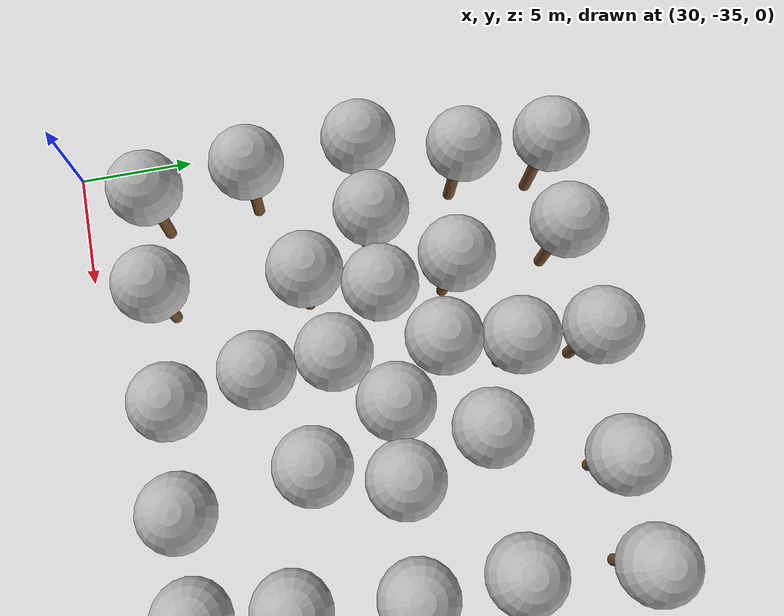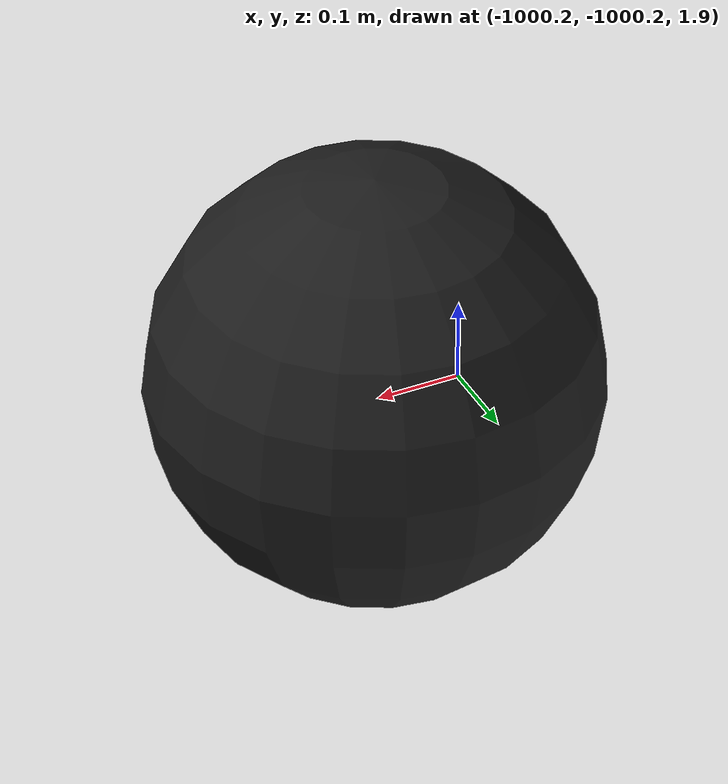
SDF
<sdf version="1.7">
 <world name="default">
  <plugin name="mrs_gazebo_static_transform_republisher_plugin" filename="libMrsGazeboCommonResources_StaticTransformRepublisher.so"/>
  <spherical_coordinates>
   <surface_model>EARTH_WGS84</surface_model>
   <latitude_deg>47.3977</latitude_deg>
   <longitude_deg>8.54559</longitude_deg>
   <elevation>0</elevation>
   <heading_deg>0</heading_deg>
  </spherical_coordinates>
  <physics name="default_physics" default="0" type="ode">
   <ode>
    <solver>
     <type>quick</type>
     <iters>10</iters>
     <sor>1.3</sor>
     <use_dynamic_moi_rescaling>0</use_dynamic_moi_rescaling>
    </solver>
    <constraints>
     <cfm>0</cfm>
     <erp>0.2</erp>
     <contact_max_correcting_vel>1000</contact_max_correcting_vel>
     <contact_surface_layer>0.001</contact_surface_layer>
    </constraints>
   </ode>
   <max_step_size>0.004</max_step_size>
   <real_time_factor>1</real_time_factor>
   <real_time_update_rate>250</real_time_update_rate>
  </physics>
  <scene><shadows>0</shadows><ambient>0.4 0.4 0.4 1</ambient><background>0.7 0.7 0.7 1</background></scene>
  <light name="sun" type="directional">
   <pose>0 0 1000 0.4 0.2 0</pose>
   <diffuse>1 1 1 1</diffuse>
   <specular>0.6 0.6 0.6 1</specular>
   <direction>0.1 0.1 -0.9</direction>
   <attenuation>
    <range>20</range>
    <constant>0.5</constant>
    <linear>0.01</linear>
    <quadratic>0.001</quadratic>
   </attenuation>
   <spot><inner_angle>0</inner_angle><outer_angle>0</outer_angle><falloff>0</falloff></spot>
  </light>
  <model name="the_void">
   <static>1</static>
   <link name="link">
    <pose>0 0 0.1 0 -0 0</pose>
    <visual name="the_void">
     <pose>0 0 2 0 -0 0</pose>
     <geometry><sphere><radius>0.25</radius></sphere></geometry>
     <material>
      <script><uri>file://media/materials/scripts/Gazebo.material</uri><name>Gazebo/Black</name></script>
     </material>
    </visual>
   </link>
   <pose>-1000 -1000 0 0 -0 0</pose>
  </model>
  <plugin name="mrs_gazebo_rviz_cam_synchronizer" filename="libMrsGazeboCommonResources_RvizCameraSynchronizer.so">
   <target_frame_id>gazebo_user_camera</target_frame_id>
   <world_origin_frame_id>uav1/gps_origin</world_origin_frame_id>
   <frame_to_follow>uav1</frame_to_follow>
  </plugin>
  <gravity>0 0 -9.8066</gravity>
  <magnetic_field>6e-06 2.3e-05 -4.2e-05</magnetic_field>
  <atmosphere type="adiabatic"/>
  <model name="tree_red_0">
   <static>1</static>
   <link name="link">
    <pose>0 0 0.1 0 -0 0</pose>
    <inertial>
     <mass>666</mass>
     <inertia>
      <ixx>0.0861167</ixx>
      <ixy>0</ixy>
      <ixz>0</ixz>
      <iyy>0.0861167</iyy>
      <iyz>0</iyz>
      <izz>0.0861167</izz>
     </inertia>
    </inertial>
    <collision name="collision_trunk">
     <pose>0 0 2 0 -0 0</pose>
     <geometry><cylinder><radius>0.25</radius><length>4</length></cylinder></geometry>
     <surface>
      <contact>
       <poissons_ratio>0.347</poissons_ratio>
       <elastic_modulus>8.8e+09</elastic_modulus>
       <ode><kp>100000</kp><kd>100</kd><max_vel>100</max_vel><min_depth>0.001</min_depth></ode>
      </contact>
      <friction>
       <torsional>
        <coefficient>1</coefficient>
        <use_patch_radius>0</use_patch_radius>
        <surface_radius>0.01</surface_radius>
       </torsional>
      </friction>
     </surface>
    </collision>
    <collision name="collision_treetop">
     <pose>0 0 5.2 0 -0 0</pose>
     <geometry><sphere><radius>1.5</radius></sphere></geometry>
     <surface>
      <contact>
       <poissons_ratio>0.347</poissons_ratio>
       <elastic_modulus>8.8e+09</elastic_modulus>
       <ode><kp>100000</kp><kd>100</kd><max_vel>100</max_vel><min_depth>0.001</min_depth></ode>
      </contact>
      <friction>
       <torsional>
        <coefficient>1</coefficient>
        <use_patch_radius>0</use_patch_radius>
        <surface_radius>0.01</surface_radius>
       </torsional>
      </friction>
     </surface>
    </collision>
    <visual name="trunk">
     <pose>0 0 2 0 -0 0</pose>
     <geometry><cylinder><radius>0.25</radius><length>4</length></cylinder></geometry>
     <material>
      <script>
       <uri>model://MRS_tree_simples_fire/scripts</uri>
       <uri>model://MRS_tree_simples_fire/materials/textures</uri>
       <name>MRS_tree_simples_fire/Trunk</name>
      </script>
     </material>
    </visual>
    <visual name="treetop">
     <pose>0 0 5.2 0 -0 0</pose>
     <geometry><sphere><radius>1.5</radius></sphere></geometry>
     <material>
      <script>
       <uri>model://MRS_tree_simples_fire/scripts</uri>
       <uri>model://MRS_tree_simples_fire/materials/textures</uri>
       <name>MRS_tree_simples_fire/Treetop</name>
      </script>
     </material>
    </visual>
   </link>
   <pose>41.2461 -20.9723 0 0 -0 0</pose>
  </model>
  <model name="tree_red_1">
   <static>1</static>
   <link name="link">
    <pose>0 0 0.1 0 -0 0</pose>
    <inertial>
     <mass>666</mass>
     <inertia>
      <ixx>0.0861167</ixx>
      <ixy>0</ixy>
      <ixz>0</ixz>
      <iyy>0.0861167</iyy>
      <iyz>0</iyz>
      <izz>0.0861167</izz>
     </inertia>
    </inertial>
    <collision name="collision_trunk">
     <pose>0 0 2 0 -0 0</pose>
     <geometry><cylinder><radius>0.25</radius><length>4</length></cylinder></geometry>
     <surface>
      <contact>
       <poissons_ratio>0.347</poissons_ratio>
       <elastic_modulus>8.8e+09</elastic_modulus>
       <ode><kp>100000</kp><kd>100</kd><max_vel>100</max_vel><min_depth>0.001</min_depth></ode>
      </contact>
      <friction>
       <torsional>
        <coefficient>1</coefficient>
        <use_patch_radius>0</use_patch_radius>
        <surface_radius>0.01</surface_radius>
       </torsional>
      </friction>
     </surface>
    </collision>
    <collision name="collision_treetop">
     <pose>0 0 5.2 0 -0 0</pose>
     <geometry><sphere><radius>1.5</radius></sphere></geometry>
     <surface>
      <contact>
       <poissons_ratio>0.347</poissons_ratio>
       <elastic_modulus>8.8e+09</elastic_modulus>
       <ode><kp>100000</kp><kd>100</kd><max_vel>100</max_vel><min_depth>0.001</min_depth></ode>
      </contact>
      <friction>
       <torsional>
        <coefficient>1</coefficient>
        <use_patch_radius>0</use_patch_radius>
        <surface_radius>0.01</surface_radius>
       </torsional>
      </friction>
     </surface>
    </collision>
    <visual name="trunk">
     <pose>0 0 2 0 -0 0</pose>
     <geometry><cylinder><radius>0.25</radius><length>4</length></cylinder></geometry>
     <material>
      <script>
       <uri>model://MRS_tree_simples_fire/scripts</uri>
       <uri>model://MRS_tree_simples_fire/materials/textures</uri>
       <name>MRS_tree_simples_fire/Trunk</name>
      </script>
     </material>
    </visual>
    <visual name="treetop">
     <pose>0 0 5.2 0 -0 0</pose>
     <geometry><sphere><radius>1.5</radius></sphere></geometry>
     <material>
      <script>
       <uri>model://MRS_tree_simples_fire/scripts</uri>
       <uri>model://MRS_tree_simples_fire/materials/textures</uri>
       <name>MRS_tree_simples_fire/Treetop</name>
      </script>
     </material>
    </visual>
   </link>
   <pose>43.3385 -23.2266 0 0 -0 0</pose>
  </model>
  <model name="tree_red_2">
   <static>1</static>
   <link name="link">
    <pose>0 0 0.1 0 -0 0</pose>
    <inertial>
     <mass>666</mass>
     <inertia>
      <ixx>0.0861167</ixx>
      <ixy>0</ixy>
      <ixz>0</ixz>
      <iyy>0.0861167</iyy>
      <iyz>0</iyz>
      <izz>0.0861167</izz>
     </inertia>
    </inertial>
    <collision name="collision_trunk">
     <pose>0 0 2 0 -0 0</pose>
     <geometry><cylinder><radius>0.25</radius><length>4</length></cylinder></geometry>
     <surface>
      <contact>
       <poissons_ratio>0.347</poissons_ratio>
       <elastic_modulus>8.8e+09</elastic_modulus>
       <ode><kp>100000</kp><kd>100</kd><max_vel>100</max_vel><min_depth>0.001</min_depth></ode>
      </contact>
      <friction>
       <torsional>
        <coefficient>1</coefficient>
        <use_patch_radius>0</use_patch_radius>
        <surface_radius>0.01</surface_radius>
       </torsional>
      </friction>
     </surface>
    </collision>
    <collision name="collision_treetop">
     <pose>0 0 5.2 0 -0 0</pose>
     <geometry><sphere><radius>1.5</radius></sphere></geometry>
     <surface>
      <contact>
       <poissons_ratio>0.347</poissons_ratio>
       <elastic_modulus>8.8e+09</elastic_modulus>
       <ode><kp>100000</kp><kd>100</kd><max_vel>100</max_vel><min_depth>0.001</min_depth></ode>
      </contact>
      <friction>
       <torsional>
        <coefficient>1</coefficient>
        <use_patch_radius>0</use_patch_radius>
        <surface_radius>0.01</surface_radius>
       </torsional>
      </friction>
     </surface>
    </collision>
    <visual name="trunk">
     <pose>0 0 2 0 -0 0</pose>
     <geometry><cylinder><radius>0.25</radius><length>4</length></cylinder></geometry>
     <material>
      <script>
       <uri>model://MRS_tree_simples_fire/scripts</uri>
       <uri>model://MRS_tree_simples_fire/materials/textures</uri>
       <name>MRS_tree_simples_fire/Trunk</name>
      </script>
     </material>
    </visual>
    <visual name="treetop">
     <pose>0 0 5.2 0 -0 0</pose>
     <geometry><sphere><radius>1.5</radius></sphere></geometry>
     <material>
      <script>
       <uri>model://MRS_tree_simples_fire/scripts</uri>
       <uri>model://MRS_tree_simples_fire/materials/textures</uri>
       <name>MRS_tree_simples_fire/Treetop</name>
      </script>
     </material>
    </visual>
   </link>
   <pose>38.7483 -22.9542 0.02686 0 -0 0</pose>
  </model>
  <model name="tree_yellow">
   <static>1</static>
   <link name="link">
    <pose>0 0 0.1 0 -0 0</pose>
    <inertial>
     <mass>666</mass>
     <inertia>
      <ixx>0.0861167</ixx>
      <ixy>0</ixy>
      <ixz>0</ixz>
      <iyy>0.0861167</iyy>
      <iyz>0</iyz>
      <izz>0.0861167</izz>
     </inertia>
    </inertial>
    <collision name="collision_trunk">
     <pose>0 0 2 0 -0 0</pose>
     <geometry><cylinder><radius>0.25</radius><length>4</length></cylinder></geometry>
     <surface>
      <contact>
       <poissons_ratio>0.347</poissons_ratio>
       <elastic_modulus>8.8e+09</elastic_modulus>
       <ode><kp>100000</kp><kd>100</kd><max_vel>100</max_vel><min_depth>0.001</min_depth></ode>
      </contact>
      <friction>
       <torsional>
        <coefficient>1</coefficient>
        <use_patch_radius>0</use_patch_radius>
        <surface_radius>0.01</surface_radius>
       </torsional>
      </friction>
     </surface>
    </collision>
    <collision name="collision_treetop">
     <pose>0 0 5.2 0 -0 0</pose>
     <geometry><sphere><radius>1.5</radius></sphere></geometry>
     <surface>
      <contact>
       <poissons_ratio>0.347</poissons_ratio>
       <elastic_modulus>8.8e+09</elastic_modulus>
       <ode><kp>100000</kp><kd>100</kd><max_vel>100</max_vel><min_depth>0.001</min_depth></ode>
      </contact>
      <friction>
       <torsional>
        <coefficient>1</coefficient>
        <use_patch_radius>0</use_patch_radius>
        <surface_radius>0.01</surface_radius>
       </torsional>
      </friction>
     </surface>
    </collision>
    <visual name="trunk">
     <pose>0 0 2 0 -0 0</pose>
     <geometry><cylinder><radius>0.25</radius><length>4</length></cylinder></geometry>
     <material>
      <script>
       <uri>model://MRS_tree_simples_close/scripts</uri>
       <uri>model://MRS_tree_simples_close/materials/textures</uri>
       <name>MRS_tree_simples_close/Trunk</name>
      </script>
     </material>
    </visual>
    <visual name="treetop">
     <pose>0 0 5.2 0 -0 0</pose>
     <geometry><sphere><radius>1.5</radius></sphere></geometry>
     <material>
      <script>
       <uri>model://MRS_tree_simples_close/scripts</uri>
       <uri>model://MRS_tree_simples_close/materials/textures</uri>
       <name>MRS_tree_simples_close/Treetop</name>
      </script>
     </material>
    </visual>
   </link>
   <pose>44.9168 -19.9536 0 0 -0 0</pose>
  </model>
  <model name="tree_yellow_0">
   <static>1</static>
   <link name="link">
    <pose>0 0 0.1 0 -0 0</pose>
    <inertial>
     <mass>666</mass>
     <inertia>
      <ixx>0.0861167</ixx>
      <ixy>0</ixy>
      <ixz>0</ixz>
      <iyy>0.0861167</iyy>
      <iyz>0</iyz>
      <izz>0.0861167</izz>
     </inertia>
    </inertial>
    <collision name="collision_trunk">
     <pose>0 0 2 0 -0 0</pose>
     <geometry><cylinder><radius>0.25</radius><length>4</length></cylinder></geometry>
     <surface>
      <contact>
       <poissons_ratio>0.347</poissons_ratio>
       <elastic_modulus>8.8e+09</elastic_modulus>
       <ode><kp>100000</kp><kd>100</kd><max_vel>100</max_vel><min_depth>0.001</min_depth></ode>
      </contact>
      <friction>
       <torsional>
        <coefficient>1</coefficient>
        <use_patch_radius>0</use_patch_radius>
        <surface_radius>0.01</surface_radius>
       </torsional>
      </friction>
     </surface>
    </collision>
    <collision name="collision_treetop">
     <pose>0 0 5.2 0 -0 0</pose>
     <geometry><sphere><radius>1.5</radius></sphere></geometry>
     <surface>
      <contact>
       <poissons_ratio>0.347</poissons_ratio>
       <elastic_modulus>8.8e+09</elastic_modulus>
       <ode><kp>100000</kp><kd>100</kd><max_vel>100</max_vel><min_depth>0.001</min_depth></ode>
      </contact>
      <friction>
       <torsional>
        <coefficient>1</coefficient>
        <use_patch_radius>0</use_patch_radius>
        <surface_radius>0.01</surface_radius>
       </torsional>
      </friction>
     </surface>
    </collision>
    <visual name="trunk">
     <pose>0 0 2 0 -0 0</pose>
     <geometry><cylinder><radius>0.25</radius><length>4</length></cylinder></geometry>
     <material>
      <script>
       <uri>model://MRS_tree_simples_close/scripts</uri>
       <uri>model://MRS_tree_simples_close/materials/textures</uri>
       <name>MRS_tree_simples_close/Trunk</name>
      </script>
     </material>
    </visual>
    <visual name="treetop">
     <pose>0 0 5.2 0 -0 0</pose>
     <geometry><sphere><radius>1.5</radius></sphere></geometry>
     <material>
      <script>
       <uri>model://MRS_tree_simples_close/scripts</uri>
       <uri>model://MRS_tree_simples_close/materials/textures</uri>
       <name>MRS_tree_simples_close/Treetop</name>
      </script>
     </material>
    </visual>
   </link>
   <pose>46.1899 -23.4258 0 0 -0 0</pose>
  </model>
  <model name="tree_red_3">
   <static>1</static>
   <link name="link">
    <pose>0 0 0.1 0 -0 0</pose>
    <inertial>
     <mass>666</mass>
     <inertia>
      <ixx>0.0861167</ixx>
      <ixy>0</ixy>
      <ixz>0</ixz>
      <iyy>0.0861167</iyy>
      <iyz>0</iyz>
      <izz>0.0861167</izz>
     </inertia>
    </inertial>
    <collision name="collision_trunk">
     <pose>0 0 2 0 -0 0</pose>
     <geometry><cylinder><radius>0.25</radius><length>4</length></cylinder></geometry>
     <surface>
      <contact>
       <poissons_ratio>0.347</poissons_ratio>
       <elastic_modulus>8.8e+09</elastic_modulus>
       <ode><kp>100000</kp><kd>100</kd><max_vel>100</max_vel><min_depth>0.001</min_depth></ode>
      </contact>
      <friction>
       <torsional>
        <coefficient>1</coefficient>
        <use_patch_radius>0</use_patch_radius>
        <surface_radius>0.01</surface_radius>
       </torsional>
      </friction>
     </surface>
    </collision>
    <collision name="collision_treetop">
     <pose>0 0 5.2 0 -0 0</pose>
     <geometry><sphere><radius>1.5</radius></sphere></geometry>
     <surface>
      <contact>
       <poissons_ratio>0.347</poissons_ratio>
       <elastic_modulus>8.8e+09</elastic_modulus>
       <ode><kp>100000</kp><kd>100</kd><max_vel>100</max_vel><min_depth>0.001</min_depth></ode>
      </contact>
      <friction>
       <torsional>
        <coefficient>1</coefficient>
        <use_patch_radius>0</use_patch_radius>
        <surface_radius>0.01</surface_radius>
       </torsional>
      </friction>
     </surface>
    </collision>
    <visual name="trunk">
     <pose>0 0 2 0 -0 0</pose>
     <geometry><cylinder><radius>0.25</radius><length>4</length></cylinder></geometry>
     <material>
      <script>
       <uri>model://MRS_tree_simples_fire/scripts</uri>
       <uri>model://MRS_tree_simples_fire/materials/textures</uri>
       <name>MRS_tree_simples_fire/Trunk</name>
      </script>
     </material>
    </visual>
    <visual name="treetop">
     <pose>0 0 5.2 0 -0 0</pose>
     <geometry><sphere><radius>1.5</radius></sphere></geometry>
     <material>
      <script>
       <uri>model://MRS_tree_simples_fire/scripts</uri>
       <uri>model://MRS_tree_simples_fire/materials/textures</uri>
       <name>MRS_tree_simples_fire/Treetop</name>
      </script>
     </material>
    </visual>
   </link>
   <pose>41.1036 -25.1689 0 0 -0 0</pose>
  </model>
  <model name="tree_yellow_1">
   <static>1</static>
   <link name="link">
    <pose>0 0 0.1 0 -0 0</pose>
    <inertial>
     <mass>666</mass>
     <inertia>
      <ixx>0.0861167</ixx>
      <ixy>0</ixy>
      <ixz>0</ixz>
      <iyy>0.0861167</iyy>
      <iyz>0</iyz>
      <izz>0.0861167</izz>
     </inertia>
    </inertial>
    <collision name="collision_trunk">
     <pose>0 0 2 0 -0 0</pose>
     <geometry><cylinder><radius>0.25</radius><length>4</length></cylinder></geometry>
     <surface>
      <contact>
       <poissons_ratio>0.347</poissons_ratio>
       <elastic_modulus>8.8e+09</elastic_modulus>
       <ode><kp>100000</kp><kd>100</kd><max_vel>100</max_vel><min_depth>0.001</min_depth></ode>
      </contact>
      <friction>
       <torsional>
        <coefficient>1</coefficient>
        <use_patch_radius>0</use_patch_radius>
        <surface_radius>0.01</surface_radius>
       </torsional>
      </friction>
     </surface>
    </collision>
    <collision name="collision_treetop">
     <pose>0 0 5.2 0 -0 0</pose>
     <geometry><sphere><radius>1.5</radius></sphere></geometry>
     <surface>
      <contact>
       <poissons_ratio>0.347</poissons_ratio>
       <elastic_modulus>8.8e+09</elastic_modulus>
       <ode><kp>100000</kp><kd>100</kd><max_vel>100</max_vel><min_depth>0.001</min_depth></ode>
      </contact>
      <friction>
       <torsional>
        <coefficient>1</coefficient>
        <use_patch_radius>0</use_patch_radius>
        <surface_radius>0.01</surface_radius>
       </torsional>
      </friction>
     </surface>
    </collision>
    <visual name="trunk">
     <pose>0 0 2 0 -0 0</pose>
     <geometry><cylinder><radius>0.25</radius><length>4</length></cylinder></geometry>
     <material>
      <script>
       <uri>model://MRS_tree_simples_close/scripts</uri>
       <uri>model://MRS_tree_simples_close/materials/textures</uri>
       <name>MRS_tree_simples_close/Trunk</name>
      </script>
     </material>
    </visual>
    <visual name="treetop">
     <pose>0 0 5.2 0 -0 0</pose>
     <geometry><sphere><radius>1.5</radius></sphere></geometry>
     <material>
      <script>
       <uri>model://MRS_tree_simples_close/scripts</uri>
       <uri>model://MRS_tree_simples_close/materials/textures</uri>
       <name>MRS_tree_simples_close/Treetop</name>
      </script>
     </material>
    </visual>
   </link>
   <pose>35.7086 -22.7264 0 0 -0 0</pose>
  </model>
  <model name="tree_yellow_2">
   <static>1</static>
   <link name="link">
    <pose>0 0 0.1 0 -0 0</pose>
    <inertial>
     <mass>666</mass>
     <inertia>
      <ixx>0.0861167</ixx>
      <ixy>0</ixy>
      <ixz>0</ixz>
      <iyy>0.0861167</iyy>
      <iyz>0</iyz>
      <izz>0.0861167</izz>
     </inertia>
    </inertial>
    <collision name="collision_trunk">
     <pose>0 0 2 0 -0 0</pose>
     <geometry><cylinder><radius>0.25</radius><length>4</length></cylinder></geometry>
     <surface>
      <contact>
       <poissons_ratio>0.347</poissons_ratio>
       <elastic_modulus>8.8e+09</elastic_modulus>
       <ode><kp>100000</kp><kd>100</kd><max_vel>100</max_vel><min_depth>0.001</min_depth></ode>
      </contact>
      <friction>
       <torsional>
        <coefficient>1</coefficient>
        <use_patch_radius>0</use_patch_radius>
        <surface_radius>0.01</surface_radius>
       </torsional>
      </friction>
     </surface>
    </collision>
    <collision name="collision_treetop">
     <pose>0 0 5.2 0 -0 0</pose>
     <geometry><sphere><radius>1.5</radius></sphere></geometry>
     <surface>
      <contact>
       <poissons_ratio>0.347</poissons_ratio>
       <elastic_modulus>8.8e+09</elastic_modulus>
       <ode><kp>100000</kp><kd>100</kd><max_vel>100</max_vel><min_depth>0.001</min_depth></ode>
      </contact>
      <friction>
       <torsional>
        <coefficient>1</coefficient>
        <use_patch_radius>0</use_patch_radius>
        <surface_radius>0.01</surface_radius>
       </torsional>
      </friction>
     </surface>
    </collision>
    <visual name="trunk">
     <pose>0 0 2 0 -0 0</pose>
     <geometry><cylinder><radius>0.25</radius><length>4</length></cylinder></geometry>
     <material>
      <script>
       <uri>model://MRS_tree_simples_close/scripts</uri>
       <uri>model://MRS_tree_simples_close/materials/textures</uri>
       <name>MRS_tree_simples_close/Trunk</name>
      </script>
     </material>
    </visual>
    <visual name="treetop">
     <pose>0 0 5.2 0 -0 0</pose>
     <geometry><sphere><radius>1.5</radius></sphere></geometry>
     <material>
      <script>
       <uri>model://MRS_tree_simples_close/scripts</uri>
       <uri>model://MRS_tree_simples_close/materials/textures</uri>
       <name>MRS_tree_simples_close/Treetop</name>
      </script>
     </material>
    </visual>
   </link>
   <pose>41.7202 -18.1162 0 0 -0 0</pose>
  </model>
  <model name="tree_yellow_3">
   <static>1</static>
   <link name="link">
    <pose>0 0 0.1 0 -0 0</pose>
    <inertial>
     <mass>666</mass>
     <inertia>
      <ixx>0.0861167</ixx>
      <ixy>0</ixy>
      <ixz>0</ixz>
      <iyy>0.0861167</iyy>
      <iyz>0</iyz>
      <izz>0.0861167</izz>
     </inertia>
    </inertial>
    <collision name="collision_trunk">
     <pose>0 0 2 0 -0 0</pose>
     <geometry><cylinder><radius>0.25</radius><length>4</length></cylinder></geometry>
     <surface>
      <contact>
       <poissons_ratio>0.347</poissons_ratio>
       <elastic_modulus>8.8e+09</elastic_modulus>
       <ode><kp>100000</kp><kd>100</kd><max_vel>100</max_vel><min_depth>0.001</min_depth></ode>
      </contact>
      <friction>
       <torsional>
        <coefficient>1</coefficient>
        <use_patch_radius>0</use_patch_radius>
        <surface_radius>0.01</surface_radius>
       </torsional>
      </friction>
     </surface>
    </collision>
    <collision name="collision_treetop">
     <pose>0 0 5.2 0 -0 0</pose>
     <geometry><sphere><radius>1.5</radius></sphere></geometry>
     <surface>
      <contact>
       <poissons_ratio>0.347</poissons_ratio>
       <elastic_modulus>8.8e+09</elastic_modulus>
       <ode><kp>100000</kp><kd>100</kd><max_vel>100</max_vel><min_depth>0.001</min_depth></ode>
      </contact>
      <friction>
       <torsional>
        <coefficient>1</coefficient>
        <use_patch_radius>0</use_patch_radius>
        <surface_radius>0.01</surface_radius>
       </torsional>
      </friction>
     </surface>
    </collision>
    <visual name="trunk">
     <pose>0 0 2 0 -0 0</pose>
     <geometry><cylinder><radius>0.25</radius><length>4</length></cylinder></geometry>
     <material>
      <script>
       <uri>model://MRS_tree_simples_close/scripts</uri>
       <uri>model://MRS_tree_simples_close/materials/textures</uri>
       <name>MRS_tree_simples_close/Trunk</name>
      </script>
     </material>
    </visual>
    <visual name="treetop">
     <pose>0 0 5.2 0 -0 0</pose>
     <geometry><sphere><radius>1.5</radius></sphere></geometry>
     <material>
      <script>
       <uri>model://MRS_tree_simples_close/scripts</uri>
       <uri>model://MRS_tree_simples_close/materials/textures</uri>
       <name>MRS_tree_simples_close/Treetop</name>
      </script>
     </material>
    </visual>
   </link>
   <pose>45.1185 -26.6707 0 0 -0 0</pose>
  </model>
  <model name="tree_yellow_4">
   <static>1</static>
   <link name="link">
    <pose>0 0 0.1 0 -0 0</pose>
    <inertial>
     <mass>666</mass>
     <inertia>
      <ixx>0.0861167</ixx>
      <ixy>0</ixy>
      <ixz>0</ixz>
      <iyy>0.0861167</iyy>
      <iyz>0</iyz>
      <izz>0.0861167</izz>
     </inertia>
    </inertial>
    <collision name="collision_trunk">
     <pose>0 0 2 0 -0 0</pose>
     <geometry><cylinder><radius>0.25</radius><length>4</length></cylinder></geometry>
     <surface>
      <contact>
       <poissons_ratio>0.347</poissons_ratio>
       <elastic_modulus>8.8e+09</elastic_modulus>
       <ode><kp>100000</kp><kd>100</kd><max_vel>100</max_vel><min_depth>0.001</min_depth></ode>
      </contact>
      <friction>
       <torsional>
        <coefficient>1</coefficient>
        <use_patch_radius>0</use_patch_radius>
        <surface_radius>0.01</surface_radius>
       </torsional>
      </friction>
     </surface>
    </collision>
    <collision name="collision_treetop">
     <pose>0 0 5.2 0 -0 0</pose>
     <geometry><sphere><radius>1.5</radius></sphere></geometry>
     <surface>
      <contact>
       <poissons_ratio>0.347</poissons_ratio>
       <elastic_modulus>8.8e+09</elastic_modulus>
       <ode><kp>100000</kp><kd>100</kd><max_vel>100</max_vel><min_depth>0.001</min_depth></ode>
      </contact>
      <friction>
       <torsional>
        <coefficient>1</coefficient>
        <use_patch_radius>0</use_patch_radius>
        <surface_radius>0.01</surface_radius>
       </torsional>
      </friction>
     </surface>
    </collision>
    <visual name="trunk">
     <pose>0 0 2 0 -0 0</pose>
     <geometry><cylinder><radius>0.25</radius><length>4</length></cylinder></geometry>
     <material>
      <script>
       <uri>model://MRS_tree_simples_close/scripts</uri>
       <uri>model://MRS_tree_simples_close/materials/textures</uri>
       <name>MRS_tree_simples_close/Trunk</name>
      </script>
     </material>
    </visual>
    <visual name="treetop">
     <pose>0 0 5.2 0 -0 0</pose>
     <geometry><sphere><radius>1.5</radius></sphere></geometry>
     <material>
      <script>
       <uri>model://MRS_tree_simples_close/scripts</uri>
       <uri>model://MRS_tree_simples_close/materials/textures</uri>
       <name>MRS_tree_simples_close/Treetop</name>
      </script>
     </material>
    </visual>
   </link>
   <pose>38.1334 -19.8306 0 0 -0 0</pose>
  </model>
  <model name="tree_yellow_5">
   <static>1</static>
   <link name="link">
    <pose>0 0 0.1 0 -0 0</pose>
    <inertial>
     <mass>666</mass>
     <inertia>
      <ixx>0.0861167</ixx>
      <ixy>0</ixy>
      <ixz>0</ixz>
      <iyy>0.0861167</iyy>
      <iyz>0</iyz>
      <izz>0.0861167</izz>
     </inertia>
    </inertial>
    <collision name="collision_trunk">
     <pose>0 0 2 0 -0 0</pose>
     <geometry><cylinder><radius>0.25</radius><length>4</length></cylinder></geometry>
     <surface>
      <contact>
       <poissons_ratio>0.347</poissons_ratio>
       <elastic_modulus>8.8e+09</elastic_modulus>
       <ode><kp>100000</kp><kd>100</kd><max_vel>100</max_vel><min_depth>0.001</min_depth></ode>
      </contact>
      <friction>
       <torsional>
        <coefficient>1</coefficient>
        <use_patch_radius>0</use_patch_radius>
        <surface_radius>0.01</surface_radius>
       </torsional>
      </friction>
     </surface>
    </collision>
    <collision name="collision_treetop">
     <pose>0 0 5.2 0 -0 0</pose>
     <geometry><sphere><radius>1.5</radius></sphere></geometry>
     <surface>
      <contact>
       <poissons_ratio>0.347</poissons_ratio>
       <elastic_modulus>8.8e+09</elastic_modulus>
       <ode><kp>100000</kp><kd>100</kd><max_vel>100</max_vel><min_depth>0.001</min_depth></ode>
      </contact>
      <friction>
       <torsional>
        <coefficient>1</coefficient>
        <use_patch_radius>0</use_patch_radius>
        <surface_radius>0.01</surface_radius>
       </torsional>
      </friction>
     </surface>
    </collision>
    <visual name="trunk">
     <pose>0 0 2 0 -0 0</pose>
     <geometry><cylinder><radius>0.25</radius><length>4</length></cylinder></geometry>
     <material>
      <script>
       <uri>model://MRS_tree_simples_close/scripts</uri>
       <uri>model://MRS_tree_simples_close/materials/textures</uri>
       <name>MRS_tree_simples_close/Trunk</name>
      </script>
     </material>
    </visual>
    <visual name="treetop">
     <pose>0 0 5.2 0 -0 0</pose>
     <geometry><sphere><radius>1.5</radius></sphere></geometry>
     <material>
      <script>
       <uri>model://MRS_tree_simples_close/scripts</uri>
       <uri>model://MRS_tree_simples_close/materials/textures</uri>
       <name>MRS_tree_simples_close/Treetop</name>
      </script>
     </material>
    </visual>
   </link>
   <pose>41.2566 -28.1254 0 0 -0 0</pose>
  </model>
  <model name="tree_yellow_6">
   <static>1</static>
   <link name="link">
    <pose>0 0 0.1 0 -0 0</pose>
    <inertial>
     <mass>666</mass>
     <inertia>
      <ixx>0.0861167</ixx>
      <ixy>0</ixy>
      <ixz>0</ixz>
      <iyy>0.0861167</iyy>
      <iyz>0</iyz>
      <izz>0.0861167</izz>
     </inertia>
    </inertial>
    <collision name="collision_trunk">
     <pose>0 0 2 0 -0 0</pose>
     <geometry><cylinder><radius>0.25</radius><length>4</length></cylinder></geometry>
     <surface>
      <contact>
       <poissons_ratio>0.347</poissons_ratio>
       <elastic_modulus>8.8e+09</elastic_modulus>
       <ode><kp>100000</kp><kd>100</kd><max_vel>100</max_vel><min_depth>0.001</min_depth></ode>
      </contact>
      <friction>
       <torsional>
        <coefficient>1</coefficient>
        <use_patch_radius>0</use_patch_radius>
        <surface_radius>0.01</surface_radius>
       </torsional>
      </friction>
     </surface>
    </collision>
    <collision name="collision_treetop">
     <pose>0 0 5.2 0 -0 0</pose>
     <geometry><sphere><radius>1.5</radius></sphere></geometry>
     <surface>
      <contact>
       <poissons_ratio>0.347</poissons_ratio>
       <elastic_modulus>8.8e+09</elastic_modulus>
       <ode><kp>100000</kp><kd>100</kd><max_vel>100</max_vel><min_depth>0.001</min_depth></ode>
      </contact>
      <friction>
       <torsional>
        <coefficient>1</coefficient>
        <use_patch_radius>0</use_patch_radius>
        <surface_radius>0.01</surface_radius>
       </torsional>
      </friction>
     </surface>
    </collision>
    <visual name="trunk">
     <pose>0 0 2 0 -0 0</pose>
     <geometry><cylinder><radius>0.25</radius><length>4</length></cylinder></geometry>
     <material>
      <script>
       <uri>model://MRS_tree_simples_close/scripts</uri>
       <uri>model://MRS_tree_simples_close/materials/textures</uri>
       <name>MRS_tree_simples_close/Trunk</name>
      </script>
     </material>
    </visual>
    <visual name="treetop">
     <pose>0 0 5.2 0 -0 0</pose>
     <geometry><sphere><radius>1.5</radius></sphere></geometry>
     <material>
      <script>
       <uri>model://MRS_tree_simples_close/scripts</uri>
       <uri>model://MRS_tree_simples_close/materials/textures</uri>
       <name>MRS_tree_simples_close/Treetop</name>
      </script>
     </material>
    </visual>
   </link>
   <pose>37.701 -25.7021 0 0 -0 0</pose>
  </model>
  <model name="tree_green">
   <static>1</static>
   <link name="link">
    <pose>0 0 0.1 0 -0 0</pose>
    <inertial>
     <mass>666</mass>
     <inertia>
      <ixx>0.0861167</ixx>
      <ixy>0</ixy>
      <ixz>0</ixz>
      <iyy>0.0861167</iyy>
      <iyz>0</iyz>
      <izz>0.0861167</izz>
     </inertia>
    </inertial>
    <collision name="collision_trunk">
     <pose>0 0 2 0 -0 0</pose>
     <geometry><cylinder><radius>0.25</radius><length>4</length></cylinder></geometry>
     <surface>
      <contact>
       <poissons_ratio>0.347</poissons_ratio>
       <elastic_modulus>8.8e+09</elastic_modulus>
       <ode><kp>100000</kp><kd>100</kd><max_vel>100</max_vel><min_depth>0.001</min_depth></ode>
      </contact>
      <friction>
       <torsional>
        <coefficient>1</coefficient>
        <use_patch_radius>0</use_patch_radius>
        <surface_radius>0.01</surface_radius>
       </torsional>
      </friction>
     </surface>
    </collision>
    <collision name="collision_treetop">
     <pose>0 0 5.2 0 -0 0</pose>
     <geometry><sphere><radius>1.5</radius></sphere></geometry>
     <surface>
      <contact>
       <poissons_ratio>0.347</poissons_ratio>
       <elastic_modulus>8.8e+09</elastic_modulus>
       <ode><kp>100000</kp><kd>100</kd><max_vel>100</max_vel><min_depth>0.001</min_depth></ode>
      </contact>
      <friction>
       <torsional>
        <coefficient>1</coefficient>
        <use_patch_radius>0</use_patch_radius>
        <surface_radius>0.01</surface_radius>
       </torsional>
      </friction>
     </surface>
    </collision>
    <visual name="trunk">
     <pose>0 0 2 0 -0 0</pose>
     <geometry><cylinder><radius>0.25</radius><length>4</length></cylinder></geometry>
     <material>
      <script>
       <uri>model://MRS_tree_simple/scripts</uri>
       <uri>model://MRS_tree_simple/materials/textures</uri>
       <name>MRS_tree_simple/Trunk</name>
      </script>
     </material>
    </visual>
    <visual name="treetop">
     <pose>0 0 5.2 0 -0 0</pose>
     <geometry><sphere><radius>1.5</radius></sphere></geometry>
     <material>
      <script>
       <uri>model://MRS_tree_simple/scripts</uri>
       <uri>model://MRS_tree_simple/materials/textures</uri>
       <name>MRS_tree_simple/Treetop</name>
      </script>
     </material>
    </visual>
   </link>
   <pose>41.9029 -15.006 0 0 -0 0</pose>
  </model>
  <model name="tree_green_0">
   <static>1</static>
   <link name="link">
    <pose>0 0 0.1 0 -0 0</pose>
    <inertial>
     <mass>666</mass>
     <inertia>
      <ixx>0.0861167</ixx>
      <ixy>0</ixy>
      <ixz>0</ixz>
      <iyy>0.0861167</iyy>
      <iyz>0</iyz>
      <izz>0.0861167</izz>
     </inertia>
    </inertial>
    <collision name="collision_trunk">
     <pose>0 0 2 0 -0 0</pose>
     <geometry><cylinder><radius>0.25</radius><length>4</length></cylinder></geometry>
     <surface>
      <contact>
       <poissons_ratio>0.347</poissons_ratio>
       <elastic_modulus>8.8e+09</elastic_modulus>
       <ode><kp>100000</kp><kd>100</kd><max_vel>100</max_vel><min_depth>0.001</min_depth></ode>
      </contact>
      <friction>
       <torsional>
        <coefficient>1</coefficient>
        <use_patch_radius>0</use_patch_radius>
        <surface_radius>0.01</surface_radius>
       </torsional>
      </friction>
     </surface>
    </collision>
    <collision name="collision_treetop">
     <pose>0 0 5.2 0 -0 0</pose>
     <geometry><sphere><radius>1.5</radius></sphere></geometry>
     <surface>
      <contact>
       <poissons_ratio>0.347</poissons_ratio>
       <elastic_modulus>8.8e+09</elastic_modulus>
       <ode><kp>100000</kp><kd>100</kd><max_vel>100</max_vel><min_depth>0.001</min_depth></ode>
      </contact>
      <friction>
       <torsional>
        <coefficient>1</coefficient>
        <use_patch_radius>0</use_patch_radius>
        <surface_radius>0.01</surface_radius>
       </torsional>
      </friction>
     </surface>
    </collision>
    <visual name="trunk">
     <pose>0 0 2 0 -0 0</pose>
     <geometry><cylinder><radius>0.25</radius><length>4</length></cylinder></geometry>
     <material>
      <script>
       <uri>model://MRS_tree_simple/scripts</uri>
       <uri>model://MRS_tree_simple/materials/textures</uri>
       <name>MRS_tree_simple/Trunk</name>
      </script>
     </material>
    </visual>
    <visual name="treetop">
     <pose>0 0 5.2 0 -0 0</pose>
     <geometry><sphere><radius>1.5</radius></sphere></geometry>
     <material>
      <script>
       <uri>model://MRS_tree_simple/scripts</uri>
       <uri>model://MRS_tree_simple/materials/textures</uri>
       <name>MRS_tree_simple/Treetop</name>
      </script>
     </material>
    </visual>
   </link>
   <pose>46.7596 -15.3516 0 0 -0 0</pose>
  </model>
  <model name="tree_green_1">
   <static>1</static>
   <link name="link">
    <pose>0 0 0.1 0 -0 0</pose>
    <inertial>
     <mass>666</mass>
     <inertia>
      <ixx>0.0861167</ixx>
      <ixy>0</ixy>
      <ixz>0</ixz>
      <iyy>0.0861167</iyy>
      <iyz>0</iyz>
      <izz>0.0861167</izz>
     </inertia>
    </inertial>
    <collision name="collision_trunk">
     <pose>0 0 2 0 -0 0</pose>
     <geometry><cylinder><radius>0.25</radius><length>4</length></cylinder></geometry>
     <surface>
      <contact>
       <poissons_ratio>0.347</poissons_ratio>
       <elastic_modulus>8.8e+09</elastic_modulus>
       <ode><kp>100000</kp><kd>100</kd><max_vel>100</max_vel><min_depth>0.001</min_depth></ode>
      </contact>
      <friction>
       <torsional>
        <coefficient>1</coefficient>
        <use_patch_radius>0</use_patch_radius>
        <surface_radius>0.01</surface_radius>
       </torsional>
      </friction>
     </surface>
    </collision>
    <collision name="collision_treetop">
     <pose>0 0 5.2 0 -0 0</pose>
     <geometry><sphere><radius>1.5</radius></sphere></geometry>
     <surface>
      <contact>
       <poissons_ratio>0.347</poissons_ratio>
       <elastic_modulus>8.8e+09</elastic_modulus>
       <ode><kp>100000</kp><kd>100</kd><max_vel>100</max_vel><min_depth>0.001</min_depth></ode>
      </contact>
      <friction>
       <torsional>
        <coefficient>1</coefficient>
        <use_patch_radius>0</use_patch_radius>
        <surface_radius>0.01</surface_radius>
       </torsional>
      </friction>
     </surface>
    </collision>
    <visual name="trunk">
     <pose>0 0 2 0 -0 0</pose>
     <geometry><cylinder><radius>0.25</radius><length>4</length></cylinder></geometry>
     <material>
      <script>
       <uri>model://MRS_tree_simple/scripts</uri>
       <uri>model://MRS_tree_simple/materials/textures</uri>
       <name>MRS_tree_simple/Trunk</name>
      </script>
     </material>
    </visual>
    <visual name="treetop">
     <pose>0 0 5.2 0 -0 0</pose>
     <geometry><sphere><radius>1.5</radius></sphere></geometry>
     <material>
      <script>
       <uri>model://MRS_tree_simple/scripts</uri>
       <uri>model://MRS_tree_simple/materials/textures</uri>
       <name>MRS_tree_simple/Treetop</name>
      </script>
     </material>
    </visual>
   </link>
   <pose>50.6964 -15.2724 0 0 -0 0</pose>
  </model>
  <model name="tree_green_2">
   <static>1</static>
   <link name="link">
    <pose>0 0 0.1 0 -0 0</pose>
    <inertial>
     <mass>666</mass>
     <inertia>
      <ixx>0.0861167</ixx>
      <ixy>0</ixy>
      <ixz>0</ixz>
      <iyy>0.0861167</iyy>
      <iyz>0</iyz>
      <izz>0.0861167</izz>
     </inertia>
    </inertial>
    <collision name="collision_trunk">
     <pose>0 0 2 0 -0 0</pose>
     <geometry><cylinder><radius>0.25</radius><length>4</length></cylinder></geometry>
     <surface>
      <contact>
       <poissons_ratio>0.347</poissons_ratio>
       <elastic_modulus>8.8e+09</elastic_modulus>
       <ode><kp>100000</kp><kd>100</kd><max_vel>100</max_vel><min_depth>0.001</min_depth></ode>
      </contact>
      <friction>
       <torsional>
        <coefficient>1</coefficient>
        <use_patch_radius>0</use_patch_radius>
        <surface_radius>0.01</surface_radius>
       </torsional>
      </friction>
     </surface>
    </collision>
    <collision name="collision_treetop">
     <pose>0 0 5.2 0 -0 0</pose>
     <geometry><sphere><radius>1.5</radius></sphere></geometry>
     <surface>
      <contact>
       <poissons_ratio>0.347</poissons_ratio>
       <elastic_modulus>8.8e+09</elastic_modulus>
       <ode><kp>100000</kp><kd>100</kd><max_vel>100</max_vel><min_depth>0.001</min_depth></ode>
      </contact>
      <friction>
       <torsional>
        <coefficient>1</coefficient>
        <use_patch_radius>0</use_patch_radius>
        <surface_radius>0.01</surface_radius>
       </torsional>
      </friction>
     </surface>
    </collision>
    <visual name="trunk">
     <pose>0 0 2 0 -0 0</pose>
     <geometry><cylinder><radius>0.25</radius><length>4</length></cylinder></geometry>
     <material>
      <script>
       <uri>model://MRS_tree_simple/scripts</uri>
       <uri>model://MRS_tree_simple/materials/textures</uri>
       <name>MRS_tree_simple/Trunk</name>
      </script>
     </material>
    </visual>
    <visual name="treetop">
     <pose>0 0 5.2 0 -0 0</pose>
     <geometry><sphere><radius>1.5</radius></sphere></geometry>
     <material>
      <script>
       <uri>model://MRS_tree_simple/scripts</uri>
       <uri>model://MRS_tree_simple/materials/textures</uri>
       <name>MRS_tree_simple/Treetop</name>
      </script>
     </material>
    </visual>
   </link>
   <pose>50.3334 -23.7957 0 0 -0 0</pose>
  </model>
  <model name="tree_green_3">
   <static>1</static>
   <link name="link">
    <pose>0 0 0.1 0 -0 0</pose>
    <inertial>
     <mass>666</mass>
     <inertia>
      <ixx>0.0861167</ixx>
      <ixy>0</ixy>
      <ixz>0</ixz>
      <iyy>0.0861167</iyy>
      <iyz>0</iyz>
      <izz>0.0861167</izz>
     </inertia>
    </inertial>
    <collision name="collision_trunk">
     <pose>0 0 2 0 -0 0</pose>
     <geometry><cylinder><radius>0.25</radius><length>4</length></cylinder></geometry>
     <surface>
      <contact>
       <poissons_ratio>0.347</poissons_ratio>
       <elastic_modulus>8.8e+09</elastic_modulus>
       <ode><kp>100000</kp><kd>100</kd><max_vel>100</max_vel><min_depth>0.001</min_depth></ode>
      </contact>
      <friction>
       <torsional>
        <coefficient>1</coefficient>
        <use_patch_radius>0</use_patch_radius>
        <surface_radius>0.01</surface_radius>
       </torsional>
      </friction>
     </surface>
    </collision>
    <collision name="collision_treetop">
     <pose>0 0 5.2 0 -0 0</pose>
     <geometry><sphere><radius>1.5</radius></sphere></geometry>
     <surface>
      <contact>
       <poissons_ratio>0.347</poissons_ratio>
       <elastic_modulus>8.8e+09</elastic_modulus>
       <ode><kp>100000</kp><kd>100</kd><max_vel>100</max_vel><min_depth>0.001</min_depth></ode>
      </contact>
      <friction>
       <torsional>
        <coefficient>1</coefficient>
        <use_patch_radius>0</use_patch_radius>
        <surface_radius>0.01</surface_radius>
       </torsional>
      </friction>
     </surface>
    </collision>
    <visual name="trunk">
     <pose>0 0 2 0 -0 0</pose>
     <geometry><cylinder><radius>0.25</radius><length>4</length></cylinder></geometry>
     <material>
      <script>
       <uri>model://MRS_tree_simple/scripts</uri>
       <uri>model://MRS_tree_simple/materials/textures</uri>
       <name>MRS_tree_simple/Trunk</name>
      </script>
     </material>
    </visual>
    <visual name="treetop">
     <pose>0 0 5.2 0 -0 0</pose>
     <geometry><sphere><radius>1.5</radius></sphere></geometry>
     <material>
      <script>
       <uri>model://MRS_tree_simple/scripts</uri>
       <uri>model://MRS_tree_simple/materials/textures</uri>
       <name>MRS_tree_simple/Treetop</name>
      </script>
     </material>
    </visual>
   </link>
   <pose>49.9222 -28.2383 0 0 -0 0</pose>
  </model>
  <model name="tree_green_4">
   <static>1</static>
   <link name="link">
    <pose>0 0 0.1 0 -0 0</pose>
    <inertial>
     <mass>666</mass>
     <inertia>
      <ixx>0.0861167</ixx>
      <ixy>0</ixy>
      <ixz>0</ixz>
      <iyy>0.0861167</iyy>
      <iyz>0</iyz>
      <izz>0.0861167</izz>
     </inertia>
    </inertial>
    <collision name="collision_trunk">
     <pose>0 0 2 0 -0 0</pose>
     <geometry><cylinder><radius>0.25</radius><length>4</length></cylinder></geometry>
     <surface>
      <contact>
       <poissons_ratio>0.347</poissons_ratio>
       <elastic_modulus>8.8e+09</elastic_modulus>
       <ode><kp>100000</kp><kd>100</kd><max_vel>100</max_vel><min_depth>0.001</min_depth></ode>
      </contact>
      <friction>
       <torsional>
        <coefficient>1</coefficient>
        <use_patch_radius>0</use_patch_radius>
        <surface_radius>0.01</surface_radius>
       </torsional>
      </friction>
     </surface>
    </collision>
    <collision name="collision_treetop">
     <pose>0 0 5.2 0 -0 0</pose>
     <geometry><sphere><radius>1.5</radius></sphere></geometry>
     <surface>
      <contact>
       <poissons_ratio>0.347</poissons_ratio>
       <elastic_modulus>8.8e+09</elastic_modulus>
       <ode><kp>100000</kp><kd>100</kd><max_vel>100</max_vel><min_depth>0.001</min_depth></ode>
      </contact>
      <friction>
       <torsional>
        <coefficient>1</coefficient>
        <use_patch_radius>0</use_patch_radius>
        <surface_radius>0.01</surface_radius>
       </torsional>
      </friction>
     </surface>
    </collision>
    <visual name="trunk">
     <pose>0 0 2 0 -0 0</pose>
     <geometry><cylinder><radius>0.25</radius><length>4</length></cylinder></geometry>
     <material>
      <script>
       <uri>model://MRS_tree_simple/scripts</uri>
       <uri>model://MRS_tree_simple/materials/textures</uri>
       <name>MRS_tree_simple/Trunk</name>
      </script>
     </material>
    </visual>
    <visual name="treetop">
     <pose>0 0 5.2 0 -0 0</pose>
     <geometry><sphere><radius>1.5</radius></sphere></geometry>
     <material>
      <script>
       <uri>model://MRS_tree_simple/scripts</uri>
       <uri>model://MRS_tree_simple/materials/textures</uri>
       <name>MRS_tree_simple/Treetop</name>
      </script>
     </material>
    </visual>
   </link>
   <pose>49.5625 -31.6967 0 0 -0 0</pose>
  </model>
  <model name="tree_green_5">
   <static>1</static>
   <link name="link">
    <pose>0 0 0.1 0 -0 0</pose>
    <inertial>
     <mass>666</mass>
     <inertia>
      <ixx>0.0861167</ixx>
      <ixy>0</ixy>
      <ixz>0</ixz>
      <iyy>0.0861167</iyy>
      <iyz>0</iyz>
      <izz>0.0861167</izz>
     </inertia>
    </inertial>
    <collision name="collision_trunk">
     <pose>0 0 2 0 -0 0</pose>
     <geometry><cylinder><radius>0.25</radius><length>4</length></cylinder></geometry>
     <surface>
      <contact>
       <poissons_ratio>0.347</poissons_ratio>
       <elastic_modulus>8.8e+09</elastic_modulus>
       <ode><kp>100000</kp><kd>100</kd><max_vel>100</max_vel><min_depth>0.001</min_depth></ode>
      </contact>
      <friction>
       <torsional>
        <coefficient>1</coefficient>
        <use_patch_radius>0</use_patch_radius>
        <surface_radius>0.01</surface_radius>
       </torsional>
      </friction>
     </surface>
    </collision>
    <collision name="collision_treetop">
     <pose>0 0 5.2 0 -0 0</pose>
     <geometry><sphere><radius>1.5</radius></sphere></geometry>
     <surface>
      <contact>
       <poissons_ratio>0.347</poissons_ratio>
       <elastic_modulus>8.8e+09</elastic_modulus>
       <ode><kp>100000</kp><kd>100</kd><max_vel>100</max_vel><min_depth>0.001</min_depth></ode>
      </contact>
      <friction>
       <torsional>
        <coefficient>1</coefficient>
        <use_patch_radius>0</use_patch_radius>
        <surface_radius>0.01</surface_radius>
       </torsional>
      </friction>
     </surface>
    </collision>
    <visual name="trunk">
     <pose>0 0 2 0 -0 0</pose>
     <geometry><cylinder><radius>0.25</radius><length>4</length></cylinder></geometry>
     <material>
      <script>
       <uri>model://MRS_tree_simple/scripts</uri>
       <uri>model://MRS_tree_simple/materials/textures</uri>
       <name>MRS_tree_simple/Trunk</name>
      </script>
     </material>
    </visual>
    <visual name="treetop">
     <pose>0 0 5.2 0 -0 0</pose>
     <geometry><sphere><radius>1.5</radius></sphere></geometry>
     <material>
      <script>
       <uri>model://MRS_tree_simple/scripts</uri>
       <uri>model://MRS_tree_simple/materials/textures</uri>
       <name>MRS_tree_simple/Treetop</name>
      </script>
     </material>
    </visual>
   </link>
   <pose>45.8611 -31.7234 0 0 -0 0</pose>
  </model>
  <model name="tree_green_6">
   <static>1</static>
   <link name="link">
    <pose>0 0 0.1 0 -0 0</pose>
    <inertial>
     <mass>666</mass>
     <inertia>
      <ixx>0.0861167</ixx>
      <ixy>0</ixy>
      <ixz>0</ixz>
      <iyy>0.0861167</iyy>
      <iyz>0</iyz>
      <izz>0.0861167</izz>
     </inertia>
    </inertial>
    <collision name="collision_trunk">
     <pose>0 0 2 0 -0 0</pose>
     <geometry><cylinder><radius>0.25</radius><length>4</length></cylinder></geometry>
     <surface>
      <contact>
       <poissons_ratio>0.347</poissons_ratio>
       <elastic_modulus>8.8e+09</elastic_modulus>
       <ode><kp>100000</kp><kd>100</kd><max_vel>100</max_vel><min_depth>0.001</min_depth></ode>
      </contact>
      <friction>
       <torsional>
        <coefficient>1</coefficient>
        <use_patch_radius>0</use_patch_radius>
        <surface_radius>0.01</surface_radius>
       </torsional>
      </friction>
     </surface>
    </collision>
    <collision name="collision_treetop">
     <pose>0 0 5.2 0 -0 0</pose>
     <geometry><sphere><radius>1.5</radius></sphere></geometry>
     <surface>
      <contact>
       <poissons_ratio>0.347</poissons_ratio>
       <elastic_modulus>8.8e+09</elastic_modulus>
       <ode><kp>100000</kp><kd>100</kd><max_vel>100</max_vel><min_depth>0.001</min_depth></ode>
      </contact>
      <friction>
       <torsional>
        <coefficient>1</coefficient>
        <use_patch_radius>0</use_patch_radius>
        <surface_radius>0.01</surface_radius>
       </torsional>
      </friction>
     </surface>
    </collision>
    <visual name="trunk">
     <pose>0 0 2 0 -0 0</pose>
     <geometry><cylinder><radius>0.25</radius><length>4</length></cylinder></geometry>
     <material>
      <script>
       <uri>model://MRS_tree_simple/scripts</uri>
       <uri>model://MRS_tree_simple/materials/textures</uri>
       <name>MRS_tree_simple/Trunk</name>
      </script>
     </material>
    </visual>
    <visual name="treetop">
     <pose>0 0 5.2 0 -0 0</pose>
     <geometry><sphere><radius>1.5</radius></sphere></geometry>
     <material>
      <script>
       <uri>model://MRS_tree_simple/scripts</uri>
       <uri>model://MRS_tree_simple/materials/textures</uri>
       <name>MRS_tree_simple/Treetop</name>
      </script>
     </material>
    </visual>
   </link>
   <pose>41.8231 -31.5436 0 0 -0 0</pose>
  </model>
  <model name="tree_green_7">
   <static>1</static>
   <link name="link">
    <pose>0 0 0.1 0 -0 0</pose>
    <inertial>
     <mass>666</mass>
     <inertia>
      <ixx>0.0861167</ixx>
      <ixy>0</ixy>
      <ixz>0</ixz>
      <iyy>0.0861167</iyy>
      <iyz>0</iyz>
      <izz>0.0861167</izz>
     </inertia>
    </inertial>
    <collision name="collision_trunk">
     <pose>0 0 2 0 -0 0</pose>
     <geometry><cylinder><radius>0.25</radius><length>4</length></cylinder></geometry>
     <surface>
      <contact>
       <poissons_ratio>0.347</poissons_ratio>
       <elastic_modulus>8.8e+09</elastic_modulus>
       <ode><kp>100000</kp><kd>100</kd><max_vel>100</max_vel><min_depth>0.001</min_depth></ode>
      </contact>
      <friction>
       <torsional>
        <coefficient>1</coefficient>
        <use_patch_radius>0</use_patch_radius>
        <surface_radius>0.01</surface_radius>
       </torsional>
      </friction>
     </surface>
    </collision>
    <collision name="collision_treetop">
     <pose>0 0 5.2 0 -0 0</pose>
     <geometry><sphere><radius>1.5</radius></sphere></geometry>
     <surface>
      <contact>
       <poissons_ratio>0.347</poissons_ratio>
       <elastic_modulus>8.8e+09</elastic_modulus>
       <ode><kp>100000</kp><kd>100</kd><max_vel>100</max_vel><min_depth>0.001</min_depth></ode>
      </contact>
      <friction>
       <torsional>
        <coefficient>1</coefficient>
        <use_patch_radius>0</use_patch_radius>
        <surface_radius>0.01</surface_radius>
       </torsional>
      </friction>
     </surface>
    </collision>
    <visual name="trunk">
     <pose>0 0 2 0 -0 0</pose>
     <geometry><cylinder><radius>0.25</radius><length>4</length></cylinder></geometry>
     <material>
      <script>
       <uri>model://MRS_tree_simple/scripts</uri>
       <uri>model://MRS_tree_simple/materials/textures</uri>
       <name>MRS_tree_simple/Trunk</name>
      </script>
     </material>
    </visual>
    <visual name="treetop">
     <pose>0 0 5.2 0 -0 0</pose>
     <geometry><sphere><radius>1.5</radius></sphere></geometry>
     <material>
      <script>
       <uri>model://MRS_tree_simple/scripts</uri>
       <uri>model://MRS_tree_simple/materials/textures</uri>
       <name>MRS_tree_simple/Treetop</name>
      </script>
     </material>
    </visual>
   </link>
   <pose>37.576 -15.2417 0 0 -0 0</pose>
  </model>
  <model name="tree_green_8">
   <static>1</static>
   <link name="link">
    <pose>0 0 0.1 0 -0 0</pose>
    <inertial>
     <mass>666</mass>
     <inertia>
      <ixx>0.0861167</ixx>
      <ixy>0</ixy>
      <ixz>0</ixz>
      <iyy>0.0861167</iyy>
      <iyz>0</iyz>
      <izz>0.0861167</izz>
     </inertia>
    </inertial>
    <collision name="collision_trunk">
     <pose>0 0 2 0 -0 0</pose>
     <geometry><cylinder><radius>0.25</radius><length>4</length></cylinder></geometry>
     <surface>
      <contact>
       <poissons_ratio>0.347</poissons_ratio>
       <elastic_modulus>8.8e+09</elastic_modulus>
       <ode><kp>100000</kp><kd>100</kd><max_vel>100</max_vel><min_depth>0.001</min_depth></ode>
      </contact>
      <friction>
       <torsional>
        <coefficient>1</coefficient>
        <use_patch_radius>0</use_patch_radius>
        <surface_radius>0.01</surface_radius>
       </torsional>
      </friction>
     </surface>
    </collision>
    <collision name="collision_treetop">
     <pose>0 0 5.2 0 -0 0</pose>
     <geometry><sphere><radius>1.5</radius></sphere></geometry>
     <surface>
      <contact>
       <poissons_ratio>0.347</poissons_ratio>
       <elastic_modulus>8.8e+09</elastic_modulus>
       <ode><kp>100000</kp><kd>100</kd><max_vel>100</max_vel><min_depth>0.001</min_depth></ode>
      </contact>
      <friction>
       <torsional>
        <coefficient>1</coefficient>
        <use_patch_radius>0</use_patch_radius>
        <surface_radius>0.01</surface_radius>
       </torsional>
      </friction>
     </surface>
    </collision>
    <visual name="trunk">
     <pose>0 0 2 0 -0 0</pose>
     <geometry><cylinder><radius>0.25</radius><length>4</length></cylinder></geometry>
     <material>
      <script>
       <uri>model://MRS_tree_simple/scripts</uri>
       <uri>model://MRS_tree_simple/materials/textures</uri>
       <name>MRS_tree_simple/Trunk</name>
      </script>
     </material>
    </visual>
    <visual name="treetop">
     <pose>0 0 5.2 0 -0 0</pose>
     <geometry><sphere><radius>1.5</radius></sphere></geometry>
     <material>
      <script>
       <uri>model://MRS_tree_simple/scripts</uri>
       <uri>model://MRS_tree_simple/materials/textures</uri>
       <name>MRS_tree_simple/Treetop</name>
      </script>
     </material>
    </visual>
   </link>
   <pose>33.9131 -15.066 0 0 -0 0</pose>
  </model>
  <model name="tree_green_9">
   <static>1</static>
   <link name="link">
    <pose>0 0 0.1 0 -0 0</pose>
    <inertial>
     <mass>666</mass>
     <inertia>
      <ixx>0.0861167</ixx>
      <ixy>0</ixy>
      <ixz>0</ixz>
      <iyy>0.0861167</iyy>
      <iyz>0</iyz>
      <izz>0.0861167</izz>
     </inertia>
    </inertial>
    <collision name="collision_trunk">
     <pose>0 0 2 0 -0 0</pose>
     <geometry><cylinder><radius>0.25</radius><length>4</length></cylinder></geometry>
     <surface>
      <contact>
       <poissons_ratio>0.347</poissons_ratio>
       <elastic_modulus>8.8e+09</elastic_modulus>
       <ode><kp>100000</kp><kd>100</kd><max_vel>100</max_vel><min_depth>0.001</min_depth></ode>
      </contact>
      <friction>
       <torsional>
        <coefficient>1</coefficient>
        <use_patch_radius>0</use_patch_radius>
        <surface_radius>0.01</surface_radius>
       </torsional>
      </friction>
     </surface>
    </collision>
    <collision name="collision_treetop">
     <pose>0 0 5.2 0 -0 0</pose>
     <geometry><sphere><radius>1.5</radius></sphere></geometry>
     <surface>
      <contact>
       <poissons_ratio>0.347</poissons_ratio>
       <elastic_modulus>8.8e+09</elastic_modulus>
       <ode><kp>100000</kp><kd>100</kd><max_vel>100</max_vel><min_depth>0.001</min_depth></ode>
      </contact>
      <friction>
       <torsional>
        <coefficient>1</coefficient>
        <use_patch_radius>0</use_patch_radius>
        <surface_radius>0.01</surface_radius>
       </torsional>
      </friction>
     </surface>
    </collision>
    <visual name="trunk">
     <pose>0 0 2 0 -0 0</pose>
     <geometry><cylinder><radius>0.25</radius><length>4</length></cylinder></geometry>
     <material>
      <script>
       <uri>model://MRS_tree_simple/scripts</uri>
       <uri>model://MRS_tree_simple/materials/textures</uri>
       <name>MRS_tree_simple/Trunk</name>
      </script>
     </material>
    </visual>
    <visual name="treetop">
     <pose>0 0 5.2 0 -0 0</pose>
     <geometry><sphere><radius>1.5</radius></sphere></geometry>
     <material>
      <script>
       <uri>model://MRS_tree_simple/scripts</uri>
       <uri>model://MRS_tree_simple/materials/textures</uri>
       <name>MRS_tree_simple/Treetop</name>
      </script>
     </material>
    </visual>
   </link>
   <pose>33.7098 -18.5879 0 0 -0 0</pose>
  </model>
  <model name="tree_green_10">
   <static>1</static>
   <link name="link">
    <pose>0 0 0.1 0 -0 0</pose>
    <inertial>
     <mass>666</mass>
     <inertia>
      <ixx>0.0861167</ixx>
      <ixy>0</ixy>
      <ixz>0</ixz>
      <iyy>0.0861167</iyy>
      <iyz>0</iyz>
      <izz>0.0861167</izz>
     </inertia>
    </inertial>
    <collision name="collision_trunk">
     <pose>0 0 2 0 -0 0</pose>
     <geometry><cylinder><radius>0.25</radius><length>4</length></cylinder></geometry>
     <surface>
      <contact>
       <poissons_ratio>0.347</poissons_ratio>
       <elastic_modulus>8.8e+09</elastic_modulus>
       <ode><kp>100000</kp><kd>100</kd><max_vel>100</max_vel><min_depth>0.001</min_depth></ode>
      </contact>
      <friction>
       <torsional>
        <coefficient>1</coefficient>
        <use_patch_radius>0</use_patch_radius>
        <surface_radius>0.01</surface_radius>
       </torsional>
      </friction>
     </surface>
    </collision>
    <collision name="collision_treetop">
     <pose>0 0 5.2 0 -0 0</pose>
     <geometry><sphere><radius>1.5</radius></sphere></geometry>
     <surface>
      <contact>
       <poissons_ratio>0.347</poissons_ratio>
       <elastic_modulus>8.8e+09</elastic_modulus>
       <ode><kp>100000</kp><kd>100</kd><max_vel>100</max_vel><min_depth>0.001</min_depth></ode>
      </contact>
      <friction>
       <torsional>
        <coefficient>1</coefficient>
        <use_patch_radius>0</use_patch_radius>
        <surface_radius>0.01</surface_radius>
       </torsional>
      </friction>
     </surface>
    </collision>
    <visual name="trunk">
     <pose>0 0 2 0 -0 0</pose>
     <geometry><cylinder><radius>0.25</radius><length>4</length></cylinder></geometry>
     <material>
      <script>
       <uri>model://MRS_tree_simple/scripts</uri>
       <uri>model://MRS_tree_simple/materials/textures</uri>
       <name>MRS_tree_simple/Trunk</name>
      </script>
     </material>
    </visual>
    <visual name="treetop">
     <pose>0 0 5.2 0 -0 0</pose>
     <geometry><sphere><radius>1.5</radius></sphere></geometry>
     <material>
      <script>
       <uri>model://MRS_tree_simple/scripts</uri>
       <uri>model://MRS_tree_simple/materials/textures</uri>
       <name>MRS_tree_simple/Treetop</name>
      </script>
     </material>
    </visual>
   </link>
   <pose>32.6449 -22.6672 0 0 -0 0</pose>
  </model>
  <model name="tree_green_11">
   <static>1</static>
   <link name="link">
    <pose>0 0 0.1 0 -0 0</pose>
    <inertial>
     <mass>666</mass>
     <inertia>
      <ixx>0.0861167</ixx>
      <ixy>0</ixy>
      <ixz>0</ixz>
      <iyy>0.0861167</iyy>
      <iyz>0</iyz>
      <izz>0.0861167</izz>
     </inertia>
    </inertial>
    <collision name="collision_trunk">
     <pose>0 0 2 0 -0 0</pose>
     <geometry><cylinder><radius>0.25</radius><length>4</length></cylinder></geometry>
     <surface>
      <contact>
       <poissons_ratio>0.347</poissons_ratio>
       <elastic_modulus>8.8e+09</elastic_modulus>
       <ode><kp>100000</kp><kd>100</kd><max_vel>100</max_vel><min_depth>0.001</min_depth></ode>
      </contact>
      <friction>
       <torsional>
        <coefficient>1</coefficient>
        <use_patch_radius>0</use_patch_radius>
        <surface_radius>0.01</surface_radius>
       </torsional>
      </friction>
     </surface>
    </collision>
    <collision name="collision_treetop">
     <pose>0 0 5.2 0 -0 0</pose>
     <geometry><sphere><radius>1.5</radius></sphere></geometry>
     <surface>
      <contact>
       <poissons_ratio>0.347</poissons_ratio>
       <elastic_modulus>8.8e+09</elastic_modulus>
       <ode><kp>100000</kp><kd>100</kd><max_vel>100</max_vel><min_depth>0.001</min_depth></ode>
      </contact>
      <friction>
       <torsional>
        <coefficient>1</coefficient>
        <use_patch_radius>0</use_patch_radius>
        <surface_radius>0.01</surface_radius>
       </torsional>
      </friction>
     </surface>
    </collision>
    <visual name="trunk">
     <pose>0 0 2 0 -0 0</pose>
     <geometry><cylinder><radius>0.25</radius><length>4</length></cylinder></geometry>
     <material>
      <script>
       <uri>model://MRS_tree_simple/scripts</uri>
       <uri>model://MRS_tree_simple/materials/textures</uri>
       <name>MRS_tree_simple/Trunk</name>
      </script>
     </material>
    </visual>
    <visual name="treetop">
     <pose>0 0 5.2 0 -0 0</pose>
     <geometry><sphere><radius>1.5</radius></sphere></geometry>
     <material>
      <script>
       <uri>model://MRS_tree_simple/scripts</uri>
       <uri>model://MRS_tree_simple/materials/textures</uri>
       <name>MRS_tree_simple/Treetop</name>
      </script>
     </material>
    </visual>
   </link>
   <pose>32.9282 -27.2282 0 0 -0 0</pose>
  </model>
  <model name="tree_green_12">
   <static>1</static>
   <link name="link">
    <pose>0 0 0.1 0 -0 0</pose>
    <inertial>
     <mass>666</mass>
     <inertia>
      <ixx>0.0861167</ixx>
      <ixy>0</ixy>
      <ixz>0</ixz>
      <iyy>0.0861167</iyy>
      <iyz>0</iyz>
      <izz>0.0861167</izz>
     </inertia>
    </inertial>
    <collision name="collision_trunk">
     <pose>0 0 2 0 -0 0</pose>
     <geometry><cylinder><radius>0.25</radius><length>4</length></cylinder></geometry>
     <surface>
      <contact>
       <poissons_ratio>0.347</poissons_ratio>
       <elastic_modulus>8.8e+09</elastic_modulus>
       <ode><kp>100000</kp><kd>100</kd><max_vel>100</max_vel><min_depth>0.001</min_depth></ode>
      </contact>
      <friction>
       <torsional>
        <coefficient>1</coefficient>
        <use_patch_radius>0</use_patch_radius>
        <surface_radius>0.01</surface_radius>
       </torsional>
      </friction>
     </surface>
    </collision>
    <collision name="collision_treetop">
     <pose>0 0 5.2 0 -0 0</pose>
     <geometry><sphere><radius>1.5</radius></sphere></geometry>
     <surface>
      <contact>
       <poissons_ratio>0.347</poissons_ratio>
       <elastic_modulus>8.8e+09</elastic_modulus>
       <ode><kp>100000</kp><kd>100</kd><max_vel>100</max_vel><min_depth>0.001</min_depth></ode>
      </contact>
      <friction>
       <torsional>
        <coefficient>1</coefficient>
        <use_patch_radius>0</use_patch_radius>
        <surface_radius>0.01</surface_radius>
       </torsional>
      </friction>
     </surface>
    </collision>
    <visual name="trunk">
     <pose>0 0 2 0 -0 0</pose>
     <geometry><cylinder><radius>0.25</radius><length>4</length></cylinder></geometry>
     <material>
      <script>
       <uri>model://MRS_tree_simple/scripts</uri>
       <uri>model://MRS_tree_simple/materials/textures</uri>
       <name>MRS_tree_simple/Trunk</name>
      </script>
     </material>
    </visual>
    <visual name="treetop">
     <pose>0 0 5.2 0 -0 0</pose>
     <geometry><sphere><radius>1.5</radius></sphere></geometry>
     <material>
      <script>
       <uri>model://MRS_tree_simple/scripts</uri>
       <uri>model://MRS_tree_simple/materials/textures</uri>
       <name>MRS_tree_simple/Treetop</name>
      </script>
     </material>
    </visual>
   </link>
   <pose>33.2813 -31.3253 0 0 -0 0</pose>
  </model>
  <model name="tree_green_13">
   <static>1</static>
   <link name="link">
    <pose>0 0 0.1 0 -0 0</pose>
    <inertial>
     <mass>666</mass>
     <inertia>
      <ixx>0.0861167</ixx>
      <ixy>0</ixy>
      <ixz>0</ixz>
      <iyy>0.0861167</iyy>
      <iyz>0</iyz>
      <izz>0.0861167</izz>
     </inertia>
    </inertial>
    <collision name="collision_trunk">
     <pose>0 0 2 0 -0 0</pose>
     <geometry><cylinder><radius>0.25</radius><length>4</length></cylinder></geometry>
     <surface>
      <contact>
       <poissons_ratio>0.347</poissons_ratio>
       <elastic_modulus>8.8e+09</elastic_modulus>
       <ode><kp>100000</kp><kd>100</kd><max_vel>100</max_vel><min_depth>0.001</min_depth></ode>
      </contact>
      <friction>
       <torsional>
        <coefficient>1</coefficient>
        <use_patch_radius>0</use_patch_radius>
        <surface_radius>0.01</surface_radius>
       </torsional>
      </friction>
     </surface>
    </collision>
    <collision name="collision_treetop">
     <pose>0 0 5.2 0 -0 0</pose>
     <geometry><sphere><radius>1.5</radius></sphere></geometry>
     <surface>
      <contact>
       <poissons_ratio>0.347</poissons_ratio>
       <elastic_modulus>8.8e+09</elastic_modulus>
       <ode><kp>100000</kp><kd>100</kd><max_vel>100</max_vel><min_depth>0.001</min_depth></ode>
      </contact>
      <friction>
       <torsional>
        <coefficient>1</coefficient>
        <use_patch_radius>0</use_patch_radius>
        <surface_radius>0.01</surface_radius>
       </torsional>
      </friction>
     </surface>
    </collision>
    <visual name="trunk">
     <pose>0 0 2 0 -0 0</pose>
     <geometry><cylinder><radius>0.25</radius><length>4</length></cylinder></geometry>
     <material>
      <script>
       <uri>model://MRS_tree_simple/scripts</uri>
       <uri>model://MRS_tree_simple/materials/textures</uri>
       <name>MRS_tree_simple/Trunk</name>
      </script>
     </material>
    </visual>
    <visual name="treetop">
     <pose>0 0 5.2 0 -0 0</pose>
     <geometry><sphere><radius>1.5</radius></sphere></geometry>
     <material>
      <script>
       <uri>model://MRS_tree_simple/scripts</uri>
       <uri>model://MRS_tree_simple/materials/textures</uri>
       <name>MRS_tree_simple/Treetop</name>
      </script>
     </material>
    </visual>
   </link>
   <pose>37.2241 -31.5886 0 0 -0 0</pose>
  </model>
  <model name="tree_green_1_clone">
   <static>1</static>
   <link name="link">
    <pose>0 0 0.1 0 -0 0</pose>
    <inertial>
     <mass>666</mass>
     <inertia>
      <ixx>0.0861167</ixx>
      <ixy>0</ixy>
      <ixz>0</ixz>
      <iyy>0.0861167</iyy>
      <iyz>0</iyz>
      <izz>0.0861167</izz>
     </inertia>
    </inertial>
    <collision name="collision_trunk">
     <pose>0 0 2 0 -0 0</pose>
     <geometry><cylinder><radius>0.25</radius><length>4</length></cylinder></geometry>
     <surface>
      <contact>
       <poissons_ratio>0.347</poissons_ratio>
       <elastic_modulus>8.8e+09</elastic_modulus>
       <ode><kp>100000</kp><kd>100</kd><max_vel>100</max_vel><min_depth>0.001</min_depth></ode>
      </contact>
      <friction>
       <torsional>
        <coefficient>1</coefficient>
        <use_patch_radius>0</use_patch_radius>
        <surface_radius>0.01</surface_radius>
       </torsional>
      </friction>
     </surface>
    </collision>
    <collision name="collision_treetop">
     <pose>0 0 5.2 0 -0 0</pose>
     <geometry><sphere><radius>1.5</radius></sphere></geometry>
     <surface>
      <contact>
       <poissons_ratio>0.347</poissons_ratio>
       <elastic_modulus>8.8e+09</elastic_modulus>
       <ode><kp>100000</kp><kd>100</kd><max_vel>100</max_vel><min_depth>0.001</min_depth></ode>
      </contact>
      <friction>
       <torsional>
        <coefficient>1</coefficient>
        <use_patch_radius>0</use_patch_radius>
        <surface_radius>0.01</surface_radius>
       </torsional>
      </friction>
     </surface>
    </collision>
    <visual name="trunk">
     <pose>0 0 2 0 -0 0</pose>
     <geometry><cylinder><radius>0.25</radius><length>4</length></cylinder></geometry>
     <material>
      <script>
       <uri>model://MRS_tree_simple/scripts</uri>
       <uri>model://MRS_tree_simple/materials/textures</uri>
       <name>MRS_tree_simple/Trunk</name>
      </script>
     </material>
    </visual>
    <visual name="treetop">
     <pose>0 0 5.2 0 -0 0</pose>
     <geometry><sphere><radius>1.5</radius></sphere></geometry>
     <material>
      <script>
       <uri>model://MRS_tree_simple/scripts</uri>
       <uri>model://MRS_tree_simple/materials/textures</uri>
       <name>MRS_tree_simple/Treetop</name>
      </script>
     </material>
    </visual>
   </link>
   <pose>50.202 -19.9186 0 0 -0 0</pose>
  </model>
 </world>
</sdf>
